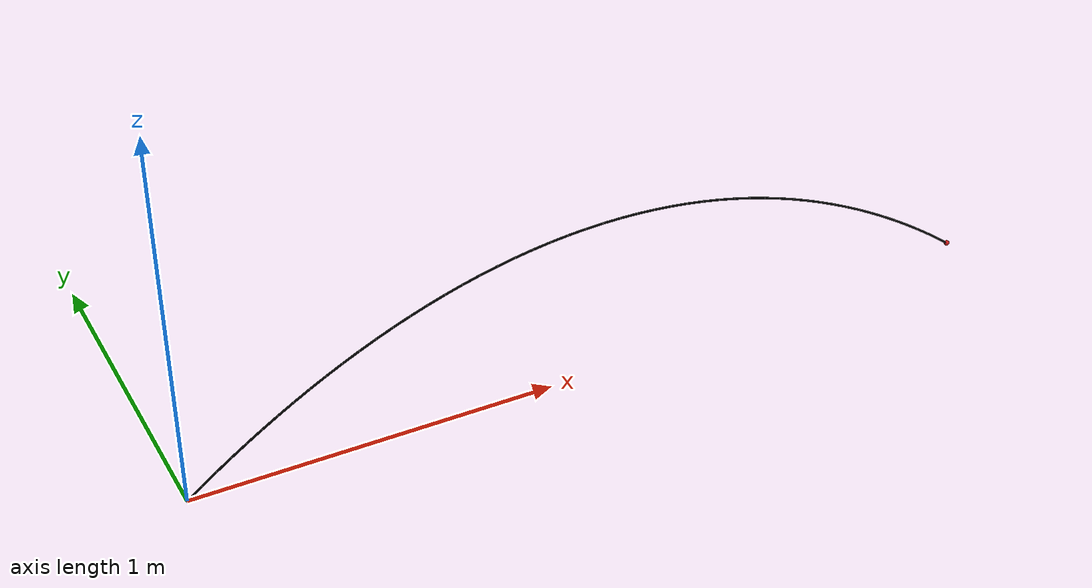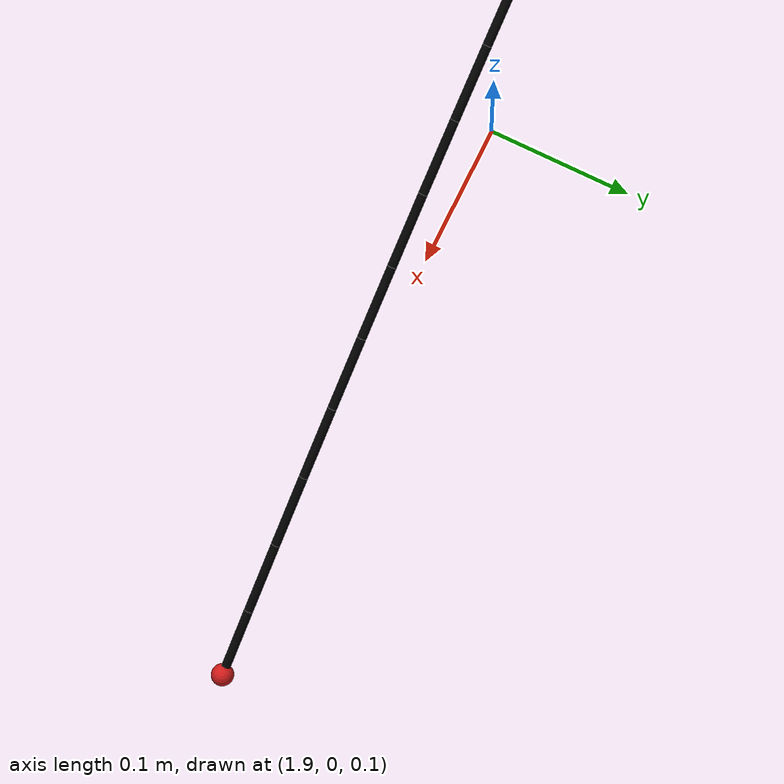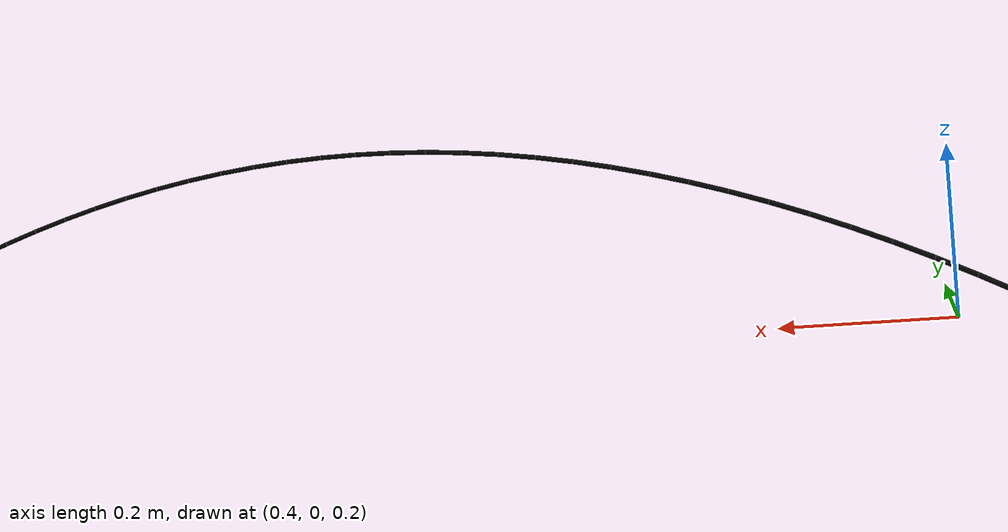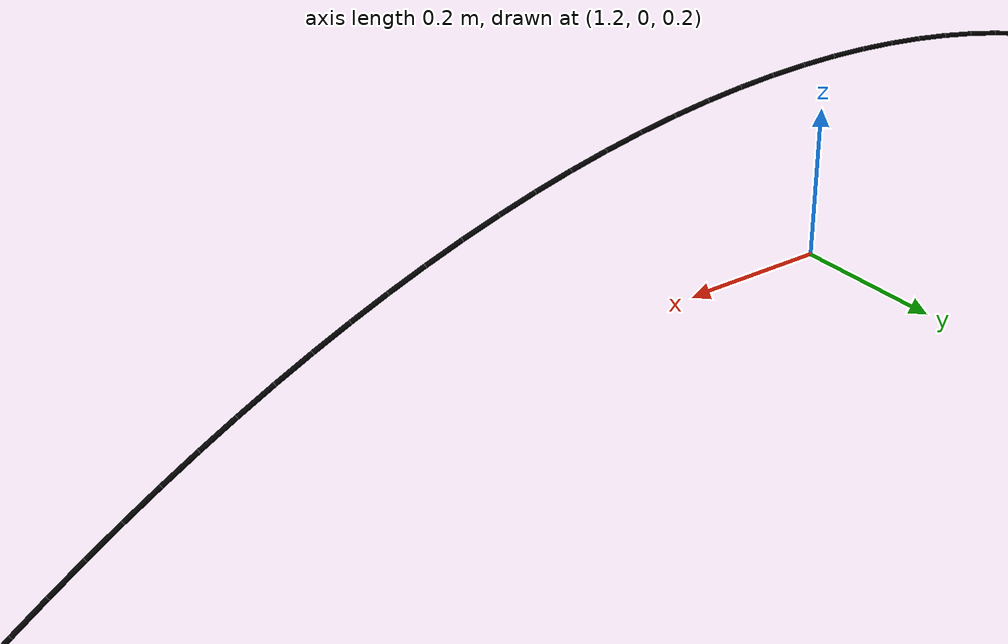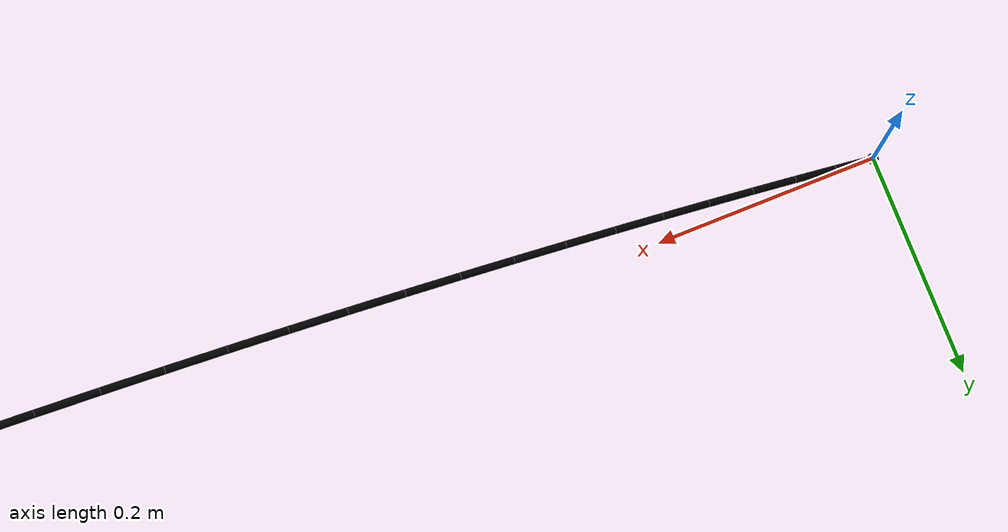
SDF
<?xml version="1.0" ?>
<sdf version="1.8">
  <model name="cabo">
    <self_collide>false</self_collide>

    <plugin filename="gz-sim-joint-state-publisher-system" name="gz::sim::systems::JointStatePublisher"/>

    <link name="raiz_cabo">
      <pose>0 0 0 0 0 0</pose>
      <inertial>
        <mass>0.02</mass>
        <inertia>
          <ixx>1e-05</ixx><ixy>0</ixy><ixz>0</ixz>
          <iyy>1e-05</iyy><iyz>0</iyz><izz>1e-05</izz>
        </inertia>
      </inertial>
      <visual name="visual_raiz">
        <geometry><sphere><radius>0.005</radius></sphere></geometry>
        <material>
          <ambient>0.1 0.1 0.1 1</ambient>
          <diffuse>0.1 0.1 0.1 1</diffuse>
        </material>
      </visual>
    </link>

      <link name="segment_1">
        <pose>0.000000 0.000000 0.000000 0 -0.653225 0.000000</pose>
        <enable_wind>false</enable_wind>
        <self_collide>false</self_collide>

        <visual name="visual">
          <pose>0.025000 0 0 0 1.5708 0</pose>
          <geometry><cylinder><radius>0.003</radius><length>0.050000</length></cylinder></geometry>
          <material>
            <ambient>0 0 0 1</ambient>
            <diffuse>0 0 0 1</diffuse>
          </material>
        </visual>
        <collision name="collision">
          <pose>0.025000 0 0 0 1.5708 0</pose>
          <geometry><cylinder><radius>0.0015</radius><length>0.030000</length></cylinder></geometry>
        </collision>

        <inertial>
          <pose>0.025000 0 0 0 0 0</pose>
          <mass>0.002000000000000001</mass>
          <inertia>
            <ixx>1e-05</ixx><ixy>0</ixy><ixz>0</ixz>
            <iyy>1e-05</iyy><iyz>0</iyz><izz>1e-05</izz>
          </inertia>
        </inertial>
      </link>

      <joint name="joint_1" type="universal">
        <parent>raiz_cabo</parent>
        <child>segment_1</child>
        <pose>0 0 0 0 0 0</pose>
        <axis>
          <xyz>0 1 0</xyz>
        <limit>
          <lower>-0.523599</lower>
          <upper>0.523599</upper>
        </limit>

          <dynamics>
            <damping>0.002</damping>
            <friction>0.0</friction>
          </dynamics>
        </axis>
        <axis2>
          <xyz>0 0 1</xyz>
        <limit>
          <lower>-0.523599</lower>
          <upper>0.523599</upper>
        </limit>

          <dynamics>
            <damping>0.002</damping>
            <friction>0.0</friction>
          </dynamics>
        </axis2>

      <sensor name="sensor_tensao_ancora" type="force_torque">
        <always_on>true</always_on>
        <update_rate>50</update_rate>
        <topic>/cabo/tensao_ancora</topic>
      </sensor>
      </joint>

      <link name="segment_2">
        <pose>0.039706 0.000000 0.030388 0 -0.636634 0.000000</pose>
        <enable_wind>false</enable_wind>
        <self_collide>false</self_collide>

        <visual name="visual">
          <pose>0.025000 0 0 0 1.5708 0</pose>
          <geometry><cylinder><radius>0.003</radius><length>0.050000</length></cylinder></geometry>
          <material>
            <ambient>0 0 0 1</ambient>
            <diffuse>0 0 0 1</diffuse>
          </material>
        </visual>
        <collision name="collision">
          <pose>0.025000 0 0 0 1.5708 0</pose>
          <geometry><cylinder><radius>0.0015</radius><length>0.030000</length></cylinder></geometry>
        </collision>

        <inertial>
          <pose>0.025000 0 0 0 0 0</pose>
          <mass>0.002</mass>
          <inertia>
            <ixx>1e-05</ixx><ixy>0</ixy><ixz>0</ixz>
            <iyy>1e-05</iyy><iyz>0</iyz><izz>1e-05</izz>
          </inertia>
        </inertial>
      </link>

      <joint name="joint_2" type="universal">
        <parent>segment_1</parent>
        <child>segment_2</child>
        <pose>0 0 0 0 0 0</pose>
        <axis>
          <xyz>0 1 0</xyz>
        <limit>
          <lower>-0.523599</lower>
          <upper>0.523599</upper>
        </limit>

          <dynamics>
            <damping>0.002</damping>
            <friction>0.0</friction>
          </dynamics>
        </axis>
        <axis2>
          <xyz>0 0 1</xyz>
        <limit>
          <lower>-0.523599</lower>
          <upper>0.523599</upper>
        </limit>

          <dynamics>
            <damping>0.002</damping>
            <friction>0.0</friction>
          </dynamics>
        </axis2>

      </joint>

      <link name="segment_3">
        <pose>0.079911 0.000000 0.060112 0 -0.619409 0.000000</pose>
        <enable_wind>false</enable_wind>
        <self_collide>false</self_collide>

        <visual name="visual">
          <pose>0.025000 0 0 0 1.5708 0</pose>
          <geometry><cylinder><radius>0.003</radius><length>0.050000</length></cylinder></geometry>
          <material>
            <ambient>0 0 0 1</ambient>
            <diffuse>0 0 0 1</diffuse>
          </material>
        </visual>
        <collision name="collision">
          <pose>0.025000 0 0 0 1.5708 0</pose>
          <geometry><cylinder><radius>0.0015</radius><length>0.030000</length></cylinder></geometry>
        </collision>

        <inertial>
          <pose>0.025000 0 0 0 0 0</pose>
          <mass>0.0019999999999999996</mass>
          <inertia>
            <ixx>1e-05</ixx><ixy>0</ixy><ixz>0</ixz>
            <iyy>1e-05</iyy><iyz>0</iyz><izz>1e-05</izz>
          </inertia>
        </inertial>
      </link>

      <joint name="joint_3" type="universal">
        <parent>segment_2</parent>
        <child>segment_3</child>
        <pose>0 0 0 0 0 0</pose>
        <axis>
          <xyz>0 1 0</xyz>
        <limit>
          <lower>-0.523599</lower>
          <upper>0.523599</upper>
        </limit>

          <dynamics>
            <damping>0.002</damping>
            <friction>0.0</friction>
          </dynamics>
        </axis>
        <axis2>
          <xyz>0 0 1</xyz>
        <limit>
          <lower>-0.523599</lower>
          <upper>0.523599</upper>
        </limit>

          <dynamics>
            <damping>0.002</damping>
            <friction>0.0</friction>
          </dynamics>
        </axis2>

      </joint>

      <link name="segment_4">
        <pose>0.120623 0.000000 0.089140 0 -0.601526 0.000000</pose>
        <enable_wind>false</enable_wind>
        <self_collide>false</self_collide>

        <visual name="visual">
          <pose>0.025000 0 0 0 1.5708 0</pose>
          <geometry><cylinder><radius>0.003</radius><length>0.050000</length></cylinder></geometry>
          <material>
            <ambient>0 0 0 1</ambient>
            <diffuse>0 0 0 1</diffuse>
          </material>
        </visual>
        <collision name="collision">
          <pose>0.025000 0 0 0 1.5708 0</pose>
          <geometry><cylinder><radius>0.0015</radius><length>0.030000</length></cylinder></geometry>
        </collision>

        <inertial>
          <pose>0.025000 0 0 0 0 0</pose>
          <mass>0.0019999999999999987</mass>
          <inertia>
            <ixx>1e-05</ixx><ixy>0</ixy><ixz>0</ixz>
            <iyy>1e-05</iyy><iyz>0</iyz><izz>1e-05</izz>
          </inertia>
        </inertial>
      </link>

      <joint name="joint_4" type="universal">
        <parent>segment_3</parent>
        <child>segment_4</child>
        <pose>0 0 0 0 0 0</pose>
        <axis>
          <xyz>0 1 0</xyz>
        <limit>
          <lower>-0.523599</lower>
          <upper>0.523599</upper>
        </limit>

          <dynamics>
            <damping>0.002</damping>
            <friction>0.0</friction>
          </dynamics>
        </axis>
        <axis2>
          <xyz>0 0 1</xyz>
        <limit>
          <lower>-0.523599</lower>
          <upper>0.523599</upper>
        </limit>

          <dynamics>
            <damping>0.002</damping>
            <friction>0.0</friction>
          </dynamics>
        </axis2>

      </joint>

      <link name="segment_5">
        <pose>0.161846 0.000000 0.117435 0 -0.582958 0.000000</pose>
        <enable_wind>false</enable_wind>
        <self_collide>false</self_collide>

        <visual name="visual">
          <pose>0.025000 0 0 0 1.5708 0</pose>
          <geometry><cylinder><radius>0.003</radius><length>0.050000</length></cylinder></geometry>
          <material>
            <ambient>0 0 0 1</ambient>
            <diffuse>0 0 0 1</diffuse>
          </material>
        </visual>
        <collision name="collision">
          <pose>0.025000 0 0 0 1.5708 0</pose>
          <geometry><cylinder><radius>0.0015</radius><length>0.030000</length></cylinder></geometry>
        </collision>

        <inertial>
          <pose>0.025000 0 0 0 0 0</pose>
          <mass>0.002</mass>
          <inertia>
            <ixx>1e-05</ixx><ixy>0</ixy><ixz>0</ixz>
            <iyy>1e-05</iyy><iyz>0</iyz><izz>1e-05</izz>
          </inertia>
        </inertial>
      </link>

      <joint name="joint_5" type="universal">
        <parent>segment_4</parent>
        <child>segment_5</child>
        <pose>0 0 0 0 0 0</pose>
        <axis>
          <xyz>0 1 0</xyz>
        <limit>
          <lower>-0.523599</lower>
          <upper>0.523599</upper>
        </limit>

          <dynamics>
            <damping>0.002</damping>
            <friction>0.0</friction>
          </dynamics>
        </axis>
        <axis2>
          <xyz>0 0 1</xyz>
        <limit>
          <lower>-0.523599</lower>
          <upper>0.523599</upper>
        </limit>

          <dynamics>
            <damping>0.002</damping>
            <friction>0.0</friction>
          </dynamics>
        </axis2>

      </joint>

      <link name="segment_6">
        <pose>0.203588 0.000000 0.144960 0 -0.563683 0.000000</pose>
        <enable_wind>false</enable_wind>
        <self_collide>false</self_collide>

        <visual name="visual">
          <pose>0.025000 0 0 0 1.5708 0</pose>
          <geometry><cylinder><radius>0.003</radius><length>0.050000</length></cylinder></geometry>
          <material>
            <ambient>0 0 0 1</ambient>
            <diffuse>0 0 0 1</diffuse>
          </material>
        </visual>
        <collision name="collision">
          <pose>0.025000 0 0 0 1.5708 0</pose>
          <geometry><cylinder><radius>0.0015</radius><length>0.030000</length></cylinder></geometry>
        </collision>

        <inertial>
          <pose>0.025000 0 0 0 0 0</pose>
          <mass>0.002000000000000001</mass>
          <inertia>
            <ixx>1e-05</ixx><ixy>0</ixy><ixz>0</ixz>
            <iyy>1e-05</iyy><iyz>0</iyz><izz>1e-05</izz>
          </inertia>
        </inertial>
      </link>

      <joint name="joint_6" type="universal">
        <parent>segment_5</parent>
        <child>segment_6</child>
        <pose>0 0 0 0 0 0</pose>
        <axis>
          <xyz>0 1 0</xyz>
        <limit>
          <lower>-0.523599</lower>
          <upper>0.523599</upper>
        </limit>

          <dynamics>
            <damping>0.002</damping>
            <friction>0.0</friction>
          </dynamics>
        </axis>
        <axis2>
          <xyz>0 0 1</xyz>
        <limit>
          <lower>-0.523599</lower>
          <upper>0.523599</upper>
        </limit>

          <dynamics>
            <damping>0.002</damping>
            <friction>0.0</friction>
          </dynamics>
        </axis2>

      </joint>

      <link name="segment_7">
        <pose>0.245853 0.000000 0.171675 0 -0.543677 0.000000</pose>
        <enable_wind>false</enable_wind>
        <self_collide>false</self_collide>

        <visual name="visual">
          <pose>0.025000 0 0 0 1.5708 0</pose>
          <geometry><cylinder><radius>0.003</radius><length>0.050000</length></cylinder></geometry>
          <material>
            <ambient>0 0 0 1</ambient>
            <diffuse>0 0 0 1</diffuse>
          </material>
        </visual>
        <collision name="collision">
          <pose>0.025000 0 0 0 1.5708 0</pose>
          <geometry><cylinder><radius>0.0015</radius><length>0.030000</length></cylinder></geometry>
        </collision>

        <inertial>
          <pose>0.025000 0 0 0 0 0</pose>
          <mass>0.0019999999999999983</mass>
          <inertia>
            <ixx>1e-05</ixx><ixy>0</ixy><ixz>0</ixz>
            <iyy>1e-05</iyy><iyz>0</iyz><izz>1e-05</izz>
          </inertia>
        </inertial>
      </link>

      <joint name="joint_7" type="universal">
        <parent>segment_6</parent>
        <child>segment_7</child>
        <pose>0 0 0 0 0 0</pose>
        <axis>
          <xyz>0 1 0</xyz>
        <limit>
          <lower>-0.523599</lower>
          <upper>0.523599</upper>
        </limit>

          <dynamics>
            <damping>0.002</damping>
            <friction>0.0</friction>
          </dynamics>
        </axis>
        <axis2>
          <xyz>0 0 1</xyz>
        <limit>
          <lower>-0.523599</lower>
          <upper>0.523599</upper>
        </limit>

          <dynamics>
            <damping>0.002</damping>
            <friction>0.0</friction>
          </dynamics>
        </axis2>

      </joint>

      <link name="segment_8">
        <pose>0.288643 0.000000 0.197539 0 -0.522918 0.000000</pose>
        <enable_wind>false</enable_wind>
        <self_collide>false</self_collide>

        <visual name="visual">
          <pose>0.025000 0 0 0 1.5708 0</pose>
          <geometry><cylinder><radius>0.003</radius><length>0.050000</length></cylinder></geometry>
          <material>
            <ambient>0 0 0 1</ambient>
            <diffuse>0 0 0 1</diffuse>
          </material>
        </visual>
        <collision name="collision">
          <pose>0.025000 0 0 0 1.5708 0</pose>
          <geometry><cylinder><radius>0.0015</radius><length>0.030000</length></cylinder></geometry>
        </collision>

        <inertial>
          <pose>0.025000 0 0 0 0 0</pose>
          <mass>0.002000000000000002</mass>
          <inertia>
            <ixx>1e-05</ixx><ixy>0</ixy><ixz>0</ixz>
            <iyy>1e-05</iyy><iyz>0</iyz><izz>1e-05</izz>
          </inertia>
        </inertial>
      </link>

      <joint name="joint_8" type="universal">
        <parent>segment_7</parent>
        <child>segment_8</child>
        <pose>0 0 0 0 0 0</pose>
        <axis>
          <xyz>0 1 0</xyz>
        <limit>
          <lower>-0.523599</lower>
          <upper>0.523599</upper>
        </limit>

          <dynamics>
            <damping>0.002</damping>
            <friction>0.0</friction>
          </dynamics>
        </axis>
        <axis2>
          <xyz>0 0 1</xyz>
        <limit>
          <lower>-0.523599</lower>
          <upper>0.523599</upper>
        </limit>

          <dynamics>
            <damping>0.002</damping>
            <friction>0.0</friction>
          </dynamics>
        </axis2>

      </joint>

      <link name="segment_9">
        <pose>0.331962 0.000000 0.222510 0 -0.501387 0.000000</pose>
        <enable_wind>false</enable_wind>
        <self_collide>false</self_collide>

        <visual name="visual">
          <pose>0.025000 0 0 0 1.5708 0</pose>
          <geometry><cylinder><radius>0.003</radius><length>0.050000</length></cylinder></geometry>
          <material>
            <ambient>0 0 0 1</ambient>
            <diffuse>0 0 0 1</diffuse>
          </material>
        </visual>
        <collision name="collision">
          <pose>0.025000 0 0 0 1.5708 0</pose>
          <geometry><cylinder><radius>0.0015</radius><length>0.030000</length></cylinder></geometry>
        </collision>

        <inertial>
          <pose>0.025000 0 0 0 0 0</pose>
          <mass>0.0020000000000000013</mass>
          <inertia>
            <ixx>1e-05</ixx><ixy>0</ixy><ixz>0</ixz>
            <iyy>1e-05</iyy><iyz>0</iyz><izz>1e-05</izz>
          </inertia>
        </inertial>
      </link>

      <joint name="joint_9" type="universal">
        <parent>segment_8</parent>
        <child>segment_9</child>
        <pose>0 0 0 0 0 0</pose>
        <axis>
          <xyz>0 1 0</xyz>
        <limit>
          <lower>-0.523599</lower>
          <upper>0.523599</upper>
        </limit>

          <dynamics>
            <damping>0.002</damping>
            <friction>0.0</friction>
          </dynamics>
        </axis>
        <axis2>
          <xyz>0 0 1</xyz>
        <limit>
          <lower>-0.523599</lower>
          <upper>0.523599</upper>
        </limit>

          <dynamics>
            <damping>0.002</damping>
            <friction>0.0</friction>
          </dynamics>
        </axis2>

      </joint>

      <link name="segment_10">
        <pose>0.375807 0.000000 0.246542 0 -0.479065 0.000000</pose>
        <enable_wind>false</enable_wind>
        <self_collide>false</self_collide>

        <visual name="visual">
          <pose>0.025000 0 0 0 1.5708 0</pose>
          <geometry><cylinder><radius>0.003</radius><length>0.050000</length></cylinder></geometry>
          <material>
            <ambient>0 0 0 1</ambient>
            <diffuse>0 0 0 1</diffuse>
          </material>
        </visual>
        <collision name="collision">
          <pose>0.025000 0 0 0 1.5708 0</pose>
          <geometry><cylinder><radius>0.0015</radius><length>0.030000</length></cylinder></geometry>
        </collision>

        <inertial>
          <pose>0.025000 0 0 0 0 0</pose>
          <mass>0.001999999999999998</mass>
          <inertia>
            <ixx>1e-05</ixx><ixy>0</ixy><ixz>0</ixz>
            <iyy>1e-05</iyy><iyz>0</iyz><izz>1e-05</izz>
          </inertia>
        </inertial>
      </link>

      <joint name="joint_10" type="universal">
        <parent>segment_9</parent>
        <child>segment_10</child>
        <pose>0 0 0 0 0 0</pose>
        <axis>
          <xyz>0 1 0</xyz>
        <limit>
          <lower>-0.523599</lower>
          <upper>0.523599</upper>
        </limit>

          <dynamics>
            <damping>0.002</damping>
            <friction>0.0</friction>
          </dynamics>
        </axis>
        <axis2>
          <xyz>0 0 1</xyz>
        <limit>
          <lower>-0.523599</lower>
          <upper>0.523599</upper>
        </limit>

          <dynamics>
            <damping>0.002</damping>
            <friction>0.0</friction>
          </dynamics>
        </axis2>

      </joint>

      <link name="segment_11">
        <pose>0.420179 0.000000 0.269589 0 -0.455939 0.000000</pose>
        <enable_wind>false</enable_wind>
        <self_collide>false</self_collide>

        <visual name="visual">
          <pose>0.025000 0 0 0 1.5708 0</pose>
          <geometry><cylinder><radius>0.003</radius><length>0.050000</length></cylinder></geometry>
          <material>
            <ambient>0 0 0 1</ambient>
            <diffuse>0 0 0 1</diffuse>
          </material>
        </visual>
        <collision name="collision">
          <pose>0.025000 0 0 0 1.5708 0</pose>
          <geometry><cylinder><radius>0.0015</radius><length>0.030000</length></cylinder></geometry>
        </collision>

        <inertial>
          <pose>0.025000 0 0 0 0 0</pose>
          <mass>0.0019999999999999983</mass>
          <inertia>
            <ixx>1e-05</ixx><ixy>0</ixy><ixz>0</ixz>
            <iyy>1e-05</iyy><iyz>0</iyz><izz>1e-05</izz>
          </inertia>
        </inertial>
      </link>

      <joint name="joint_11" type="universal">
        <parent>segment_10</parent>
        <child>segment_11</child>
        <pose>0 0 0 0 0 0</pose>
        <axis>
          <xyz>0 1 0</xyz>
        <limit>
          <lower>-0.523599</lower>
          <upper>0.523599</upper>
        </limit>

          <dynamics>
            <damping>0.002</damping>
            <friction>0.0</friction>
          </dynamics>
        </axis>
        <axis2>
          <xyz>0 0 1</xyz>
        <limit>
          <lower>-0.523599</lower>
          <upper>0.523599</upper>
        </limit>

          <dynamics>
            <damping>0.002</damping>
            <friction>0.0</friction>
          </dynamics>
        </axis2>

      </joint>

      <link name="segment_12">
        <pose>0.465071 0.000000 0.291605 0 -0.431999 0.000000</pose>
        <enable_wind>false</enable_wind>
        <self_collide>false</self_collide>

        <visual name="visual">
          <pose>0.025000 0 0 0 1.5708 0</pose>
          <geometry><cylinder><radius>0.003</radius><length>0.050000</length></cylinder></geometry>
          <material>
            <ambient>0 0 0 1</ambient>
            <diffuse>0 0 0 1</diffuse>
          </material>
        </visual>
        <collision name="collision">
          <pose>0.025000 0 0 0 1.5708 0</pose>
          <geometry><cylinder><radius>0.0015</radius><length>0.030000</length></cylinder></geometry>
        </collision>

        <inertial>
          <pose>0.025000 0 0 0 0 0</pose>
          <mass>0.001999999999999997</mass>
          <inertia>
            <ixx>1e-05</ixx><ixy>0</ixy><ixz>0</ixz>
            <iyy>1e-05</iyy><iyz>0</iyz><izz>1e-05</izz>
          </inertia>
        </inertial>
      </link>

      <joint name="joint_12" type="universal">
        <parent>segment_11</parent>
        <child>segment_12</child>
        <pose>0 0 0 0 0 0</pose>
        <axis>
          <xyz>0 1 0</xyz>
        <limit>
          <lower>-0.523599</lower>
          <upper>0.523599</upper>
        </limit>

          <dynamics>
            <damping>0.002</damping>
            <friction>0.0</friction>
          </dynamics>
        </axis>
        <axis2>
          <xyz>0 0 1</xyz>
        <limit>
          <lower>-0.523599</lower>
          <upper>0.523599</upper>
        </limit>

          <dynamics>
            <damping>0.002</damping>
            <friction>0.0</friction>
          </dynamics>
        </axis2>

      </joint>

      <link name="segment_13">
        <pose>0.510478 0.000000 0.312539 0 -0.407240 0.000000</pose>
        <enable_wind>false</enable_wind>
        <self_collide>false</self_collide>

        <visual name="visual">
          <pose>0.025000 0 0 0 1.5708 0</pose>
          <geometry><cylinder><radius>0.003</radius><length>0.050000</length></cylinder></geometry>
          <material>
            <ambient>0 0 0 1</ambient>
            <diffuse>0 0 0 1</diffuse>
          </material>
        </visual>
        <collision name="collision">
          <pose>0.025000 0 0 0 1.5708 0</pose>
          <geometry><cylinder><radius>0.0015</radius><length>0.030000</length></cylinder></geometry>
        </collision>

        <inertial>
          <pose>0.025000 0 0 0 0 0</pose>
          <mass>0.0019999999999999996</mass>
          <inertia>
            <ixx>1e-05</ixx><ixy>0</ixy><ixz>0</ixz>
            <iyy>1e-05</iyy><iyz>0</iyz><izz>1e-05</izz>
          </inertia>
        </inertial>
      </link>

      <joint name="joint_13" type="universal">
        <parent>segment_12</parent>
        <child>segment_13</child>
        <pose>0 0 0 0 0 0</pose>
        <axis>
          <xyz>0 1 0</xyz>
        <limit>
          <lower>-0.523599</lower>
          <upper>0.523599</upper>
        </limit>

          <dynamics>
            <damping>0.002</damping>
            <friction>0.0</friction>
          </dynamics>
        </axis>
        <axis2>
          <xyz>0 0 1</xyz>
        <limit>
          <lower>-0.523599</lower>
          <upper>0.523599</upper>
        </limit>

          <dynamics>
            <damping>0.002</damping>
            <friction>0.0</friction>
          </dynamics>
        </axis2>

      </joint>

      <link name="segment_14">
        <pose>0.556389 0.000000 0.332343 0 -0.381662 0.000000</pose>
        <enable_wind>false</enable_wind>
        <self_collide>false</self_collide>

        <visual name="visual">
          <pose>0.025000 0 0 0 1.5708 0</pose>
          <geometry><cylinder><radius>0.003</radius><length>0.050000</length></cylinder></geometry>
          <material>
            <ambient>0 0 0 1</ambient>
            <diffuse>0 0 0 1</diffuse>
          </material>
        </visual>
        <collision name="collision">
          <pose>0.025000 0 0 0 1.5708 0</pose>
          <geometry><cylinder><radius>0.0015</radius><length>0.030000</length></cylinder></geometry>
        </collision>

        <inertial>
          <pose>0.025000 0 0 0 0 0</pose>
          <mass>0.002000000000000004</mass>
          <inertia>
            <ixx>1e-05</ixx><ixy>0</ixy><ixz>0</ixz>
            <iyy>1e-05</iyy><iyz>0</iyz><izz>1e-05</izz>
          </inertia>
        </inertial>
      </link>

      <joint name="joint_14" type="universal">
        <parent>segment_13</parent>
        <child>segment_14</child>
        <pose>0 0 0 0 0 0</pose>
        <axis>
          <xyz>0 1 0</xyz>
        <limit>
          <lower>-0.523599</lower>
          <upper>0.523599</upper>
        </limit>

          <dynamics>
            <damping>0.002</damping>
            <friction>0.0</friction>
          </dynamics>
        </axis>
        <axis2>
          <xyz>0 0 1</xyz>
        <limit>
          <lower>-0.523599</lower>
          <upper>0.523599</upper>
        </limit>

          <dynamics>
            <damping>0.002</damping>
            <friction>0.0</friction>
          </dynamics>
        </axis2>

      </joint>

      <link name="segment_15">
        <pose>0.602791 0.000000 0.350966 0 -0.355271 0.000000</pose>
        <enable_wind>false</enable_wind>
        <self_collide>false</self_collide>

        <visual name="visual">
          <pose>0.025000 0 0 0 1.5708 0</pose>
          <geometry><cylinder><radius>0.003</radius><length>0.050000</length></cylinder></geometry>
          <material>
            <ambient>0 0 0 1</ambient>
            <diffuse>0 0 0 1</diffuse>
          </material>
        </visual>
        <collision name="collision">
          <pose>0.025000 0 0 0 1.5708 0</pose>
          <geometry><cylinder><radius>0.0015</radius><length>0.030000</length></cylinder></geometry>
        </collision>

        <inertial>
          <pose>0.025000 0 0 0 0 0</pose>
          <mass>0.001999999999999998</mass>
          <inertia>
            <ixx>1e-05</ixx><ixy>0</ixy><ixz>0</ixz>
            <iyy>1e-05</iyy><iyz>0</iyz><izz>1e-05</izz>
          </inertia>
        </inertial>
      </link>

      <joint name="joint_15" type="universal">
        <parent>segment_14</parent>
        <child>segment_15</child>
        <pose>0 0 0 0 0 0</pose>
        <axis>
          <xyz>0 1 0</xyz>
        <limit>
          <lower>-0.523599</lower>
          <upper>0.523599</upper>
        </limit>

          <dynamics>
            <damping>0.002</damping>
            <friction>0.0</friction>
          </dynamics>
        </axis>
        <axis2>
          <xyz>0 0 1</xyz>
        <limit>
          <lower>-0.523599</lower>
          <upper>0.523599</upper>
        </limit>

          <dynamics>
            <damping>0.002</damping>
            <friction>0.0</friction>
          </dynamics>
        </axis2>

      </joint>

      <link name="segment_16">
        <pose>0.649668 0.000000 0.368358 0 -0.328082 0.000000</pose>
        <enable_wind>false</enable_wind>
        <self_collide>false</self_collide>

        <visual name="visual">
          <pose>0.025000 0 0 0 1.5708 0</pose>
          <geometry><cylinder><radius>0.003</radius><length>0.050000</length></cylinder></geometry>
          <material>
            <ambient>0 0 0 1</ambient>
            <diffuse>0 0 0 1</diffuse>
          </material>
        </visual>
        <collision name="collision">
          <pose>0.025000 0 0 0 1.5708 0</pose>
          <geometry><cylinder><radius>0.0015</radius><length>0.030000</length></cylinder></geometry>
        </collision>

        <inertial>
          <pose>0.025000 0 0 0 0 0</pose>
          <mass>0.001999999999999998</mass>
          <inertia>
            <ixx>1e-05</ixx><ixy>0</ixy><ixz>0</ixz>
            <iyy>1e-05</iyy><iyz>0</iyz><izz>1e-05</izz>
          </inertia>
        </inertial>
      </link>

      <joint name="joint_16" type="universal">
        <parent>segment_15</parent>
        <child>segment_16</child>
        <pose>0 0 0 0 0 0</pose>
        <axis>
          <xyz>0 1 0</xyz>
        <limit>
          <lower>-0.523599</lower>
          <upper>0.523599</upper>
        </limit>

          <dynamics>
            <damping>0.002</damping>
            <friction>0.0</friction>
          </dynamics>
        </axis>
        <axis2>
          <xyz>0 0 1</xyz>
        <limit>
          <lower>-0.523599</lower>
          <upper>0.523599</upper>
        </limit>

          <dynamics>
            <damping>0.002</damping>
            <friction>0.0</friction>
          </dynamics>
        </axis2>

      </joint>

      <link name="segment_17">
        <pose>0.697002 0.000000 0.384470 0 -0.300117 0.000000</pose>
        <enable_wind>false</enable_wind>
        <self_collide>false</self_collide>

        <visual name="visual">
          <pose>0.025000 0 0 0 1.5708 0</pose>
          <geometry><cylinder><radius>0.003</radius><length>0.050000</length></cylinder></geometry>
          <material>
            <ambient>0 0 0 1</ambient>
            <diffuse>0 0 0 1</diffuse>
          </material>
        </visual>
        <collision name="collision">
          <pose>0.025000 0 0 0 1.5708 0</pose>
          <geometry><cylinder><radius>0.0015</radius><length>0.030000</length></cylinder></geometry>
        </collision>

        <inertial>
          <pose>0.025000 0 0 0 0 0</pose>
          <mass>0.0020000000000000018</mass>
          <inertia>
            <ixx>1e-05</ixx><ixy>0</ixy><ixz>0</ixz>
            <iyy>1e-05</iyy><iyz>0</iyz><izz>1e-05</izz>
          </inertia>
        </inertial>
      </link>

      <joint name="joint_17" type="universal">
        <parent>segment_16</parent>
        <child>segment_17</child>
        <pose>0 0 0 0 0 0</pose>
        <axis>
          <xyz>0 1 0</xyz>
        <limit>
          <lower>-0.523599</lower>
          <upper>0.523599</upper>
        </limit>

          <dynamics>
            <damping>0.002</damping>
            <friction>0.0</friction>
          </dynamics>
        </axis>
        <axis2>
          <xyz>0 0 1</xyz>
        <limit>
          <lower>-0.523599</lower>
          <upper>0.523599</upper>
        </limit>

          <dynamics>
            <damping>0.002</damping>
            <friction>0.0</friction>
          </dynamics>
        </axis2>

      </joint>

      <link name="segment_18">
        <pose>0.744767 0.000000 0.399251 0 -0.271408 0.000000</pose>
        <enable_wind>false</enable_wind>
        <self_collide>false</self_collide>

        <visual name="visual">
          <pose>0.025000 0 0 0 1.5708 0</pose>
          <geometry><cylinder><radius>0.003</radius><length>0.050000</length></cylinder></geometry>
          <material>
            <ambient>0 0 0 1</ambient>
            <diffuse>0 0 0 1</diffuse>
          </material>
        </visual>
        <collision name="collision">
          <pose>0.025000 0 0 0 1.5708 0</pose>
          <geometry><cylinder><radius>0.0015</radius><length>0.030000</length></cylinder></geometry>
        </collision>

        <inertial>
          <pose>0.025000 0 0 0 0 0</pose>
          <mass>0.0019999999999999966</mass>
          <inertia>
            <ixx>1e-05</ixx><ixy>0</ixy><ixz>0</ixz>
            <iyy>1e-05</iyy><iyz>0</iyz><izz>1e-05</izz>
          </inertia>
        </inertial>
      </link>

      <joint name="joint_18" type="universal">
        <parent>segment_17</parent>
        <child>segment_18</child>
        <pose>0 0 0 0 0 0</pose>
        <axis>
          <xyz>0 1 0</xyz>
        <limit>
          <lower>-0.523599</lower>
          <upper>0.523599</upper>
        </limit>

          <dynamics>
            <damping>0.002</damping>
            <friction>0.0</friction>
          </dynamics>
        </axis>
        <axis2>
          <xyz>0 0 1</xyz>
        <limit>
          <lower>-0.523599</lower>
          <upper>0.523599</upper>
        </limit>

          <dynamics>
            <damping>0.002</damping>
            <friction>0.0</friction>
          </dynamics>
        </axis2>

      </joint>

      <link name="segment_19">
        <pose>0.792936 0.000000 0.412656 0 -0.241994 0.000000</pose>
        <enable_wind>false</enable_wind>
        <self_collide>false</self_collide>

        <visual name="visual">
          <pose>0.025000 0 0 0 1.5708 0</pose>
          <geometry><cylinder><radius>0.003</radius><length>0.050000</length></cylinder></geometry>
          <material>
            <ambient>0 0 0 1</ambient>
            <diffuse>0 0 0 1</diffuse>
          </material>
        </visual>
        <collision name="collision">
          <pose>0.025000 0 0 0 1.5708 0</pose>
          <geometry><cylinder><radius>0.0015</radius><length>0.030000</length></cylinder></geometry>
        </collision>

        <inertial>
          <pose>0.025000 0 0 0 0 0</pose>
          <mass>0.0020000000000000035</mass>
          <inertia>
            <ixx>1e-05</ixx><ixy>0</ixy><ixz>0</ixz>
            <iyy>1e-05</iyy><iyz>0</iyz><izz>1e-05</izz>
          </inertia>
        </inertial>
      </link>

      <joint name="joint_19" type="universal">
        <parent>segment_18</parent>
        <child>segment_19</child>
        <pose>0 0 0 0 0 0</pose>
        <axis>
          <xyz>0 1 0</xyz>
        <limit>
          <lower>-0.523599</lower>
          <upper>0.523599</upper>
        </limit>

          <dynamics>
            <damping>0.002</damping>
            <friction>0.0</friction>
          </dynamics>
        </axis>
        <axis2>
          <xyz>0 0 1</xyz>
        <limit>
          <lower>-0.523599</lower>
          <upper>0.523599</upper>
        </limit>

          <dynamics>
            <damping>0.002</damping>
            <friction>0.0</friction>
          </dynamics>
        </axis2>

      </joint>

      <link name="segment_20">
        <pose>0.841480 0.000000 0.424638 0 -0.211925 0.000000</pose>
        <enable_wind>false</enable_wind>
        <self_collide>false</self_collide>

        <visual name="visual">
          <pose>0.025000 0 0 0 1.5708 0</pose>
          <geometry><cylinder><radius>0.003</radius><length>0.050000</length></cylinder></geometry>
          <material>
            <ambient>0 0 0 1</ambient>
            <diffuse>0 0 0 1</diffuse>
          </material>
        </visual>
        <collision name="collision">
          <pose>0.025000 0 0 0 1.5708 0</pose>
          <geometry><cylinder><radius>0.0015</radius><length>0.030000</length></cylinder></geometry>
        </collision>

        <inertial>
          <pose>0.025000 0 0 0 0 0</pose>
          <mass>0.0019999999999999996</mass>
          <inertia>
            <ixx>1e-05</ixx><ixy>0</ixy><ixz>0</ixz>
            <iyy>1e-05</iyy><iyz>0</iyz><izz>1e-05</izz>
          </inertia>
        </inertial>
      </link>

      <joint name="joint_20" type="universal">
        <parent>segment_19</parent>
        <child>segment_20</child>
        <pose>0 0 0 0 0 0</pose>
        <axis>
          <xyz>0 1 0</xyz>
        <limit>
          <lower>-0.523599</lower>
          <upper>0.523599</upper>
        </limit>

          <dynamics>
            <damping>0.002</damping>
            <friction>0.0</friction>
          </dynamics>
        </axis>
        <axis2>
          <xyz>0 0 1</xyz>
        <limit>
          <lower>-0.523599</lower>
          <upper>0.523599</upper>
        </limit>

          <dynamics>
            <damping>0.002</damping>
            <friction>0.0</friction>
          </dynamics>
        </axis2>

      </joint>

      <link name="segment_21">
        <pose>0.890361 0.000000 0.435155 0 -0.181262 0.000000</pose>
        <enable_wind>false</enable_wind>
        <self_collide>false</self_collide>

        <visual name="visual">
          <pose>0.025000 0 0 0 1.5708 0</pose>
          <geometry><cylinder><radius>0.003</radius><length>0.050000</length></cylinder></geometry>
          <material>
            <ambient>0 0 0 1</ambient>
            <diffuse>0 0 0 1</diffuse>
          </material>
        </visual>
        <collision name="collision">
          <pose>0.025000 0 0 0 1.5708 0</pose>
          <geometry><cylinder><radius>0.0015</radius><length>0.030000</length></cylinder></geometry>
        </collision>

        <inertial>
          <pose>0.025000 0 0 0 0 0</pose>
          <mass>0.0020000000000000013</mass>
          <inertia>
            <ixx>1e-05</ixx><ixy>0</ixy><ixz>0</ixz>
            <iyy>1e-05</iyy><iyz>0</iyz><izz>1e-05</izz>
          </inertia>
        </inertial>
      </link>

      <joint name="joint_21" type="universal">
        <parent>segment_20</parent>
        <child>segment_21</child>
        <pose>0 0 0 0 0 0</pose>
        <axis>
          <xyz>0 1 0</xyz>
        <limit>
          <lower>-0.523599</lower>
          <upper>0.523599</upper>
        </limit>

          <dynamics>
            <damping>0.002</damping>
            <friction>0.0</friction>
          </dynamics>
        </axis>
        <axis2>
          <xyz>0 0 1</xyz>
        <limit>
          <lower>-0.523599</lower>
          <upper>0.523599</upper>
        </limit>

          <dynamics>
            <damping>0.002</damping>
            <friction>0.0</friction>
          </dynamics>
        </axis2>

      </joint>

      <link name="segment_22">
        <pose>0.939542 0.000000 0.444168 0 -0.150074 0.000000</pose>
        <enable_wind>false</enable_wind>
        <self_collide>false</self_collide>

        <visual name="visual">
          <pose>0.025000 0 0 0 1.5708 0</pose>
          <geometry><cylinder><radius>0.003</radius><length>0.050000</length></cylinder></geometry>
          <material>
            <ambient>0 0 0 1</ambient>
            <diffuse>0 0 0 1</diffuse>
          </material>
        </visual>
        <collision name="collision">
          <pose>0.025000 0 0 0 1.5708 0</pose>
          <geometry><cylinder><radius>0.0015</radius><length>0.030000</length></cylinder></geometry>
        </collision>

        <inertial>
          <pose>0.025000 0 0 0 0 0</pose>
          <mass>0.002000000000000002</mass>
          <inertia>
            <ixx>1e-05</ixx><ixy>0</ixy><ixz>0</ixz>
            <iyy>1e-05</iyy><iyz>0</iyz><izz>1e-05</izz>
          </inertia>
        </inertial>
      </link>

      <joint name="joint_22" type="universal">
        <parent>segment_21</parent>
        <child>segment_22</child>
        <pose>0 0 0 0 0 0</pose>
        <axis>
          <xyz>0 1 0</xyz>
        <limit>
          <lower>-0.523599</lower>
          <upper>0.523599</upper>
        </limit>

          <dynamics>
            <damping>0.002</damping>
            <friction>0.0</friction>
          </dynamics>
        </axis>
        <axis2>
          <xyz>0 0 1</xyz>
        <limit>
          <lower>-0.523599</lower>
          <upper>0.523599</upper>
        </limit>

          <dynamics>
            <damping>0.002</damping>
            <friction>0.0</friction>
          </dynamics>
        </axis2>

      </joint>

      <link name="segment_23">
        <pose>0.988980 0.000000 0.451644 0 -0.118438 0.000000</pose>
        <enable_wind>false</enable_wind>
        <self_collide>false</self_collide>

        <visual name="visual">
          <pose>0.025000 0 0 0 1.5708 0</pose>
          <geometry><cylinder><radius>0.003</radius><length>0.050000</length></cylinder></geometry>
          <material>
            <ambient>0 0 0 1</ambient>
            <diffuse>0 0 0 1</diffuse>
          </material>
        </visual>
        <collision name="collision">
          <pose>0.025000 0 0 0 1.5708 0</pose>
          <geometry><cylinder><radius>0.0015</radius><length>0.030000</length></cylinder></geometry>
        </collision>

        <inertial>
          <pose>0.025000 0 0 0 0 0</pose>
          <mass>0.0020000000000000018</mass>
          <inertia>
            <ixx>1e-05</ixx><ixy>0</ixy><ixz>0</ixz>
            <iyy>1e-05</iyy><iyz>0</iyz><izz>1e-05</izz>
          </inertia>
        </inertial>
      </link>

      <joint name="joint_23" type="universal">
        <parent>segment_22</parent>
        <child>segment_23</child>
        <pose>0 0 0 0 0 0</pose>
        <axis>
          <xyz>0 1 0</xyz>
        <limit>
          <lower>-0.523599</lower>
          <upper>0.523599</upper>
        </limit>

          <dynamics>
            <damping>0.002</damping>
            <friction>0.0</friction>
          </dynamics>
        </axis>
        <axis2>
          <xyz>0 0 1</xyz>
        <limit>
          <lower>-0.523599</lower>
          <upper>0.523599</upper>
        </limit>

          <dynamics>
            <damping>0.002</damping>
            <friction>0.0</friction>
          </dynamics>
        </axis2>

      </joint>

      <link name="segment_24">
        <pose>1.038629 0.000000 0.457552 0 -0.086441 0.000000</pose>
        <enable_wind>false</enable_wind>
        <self_collide>false</self_collide>

        <visual name="visual">
          <pose>0.025000 0 0 0 1.5708 0</pose>
          <geometry><cylinder><radius>0.003</radius><length>0.050000</length></cylinder></geometry>
          <material>
            <ambient>0 0 0 1</ambient>
            <diffuse>0 0 0 1</diffuse>
          </material>
        </visual>
        <collision name="collision">
          <pose>0.025000 0 0 0 1.5708 0</pose>
          <geometry><cylinder><radius>0.0015</radius><length>0.030000</length></cylinder></geometry>
        </collision>

        <inertial>
          <pose>0.025000 0 0 0 0 0</pose>
          <mass>0.002000000000000006</mass>
          <inertia>
            <ixx>1e-05</ixx><ixy>0</ixy><ixz>0</ixz>
            <iyy>1e-05</iyy><iyz>0</iyz><izz>1e-05</izz>
          </inertia>
        </inertial>
      </link>

      <joint name="joint_24" type="universal">
        <parent>segment_23</parent>
        <child>segment_24</child>
        <pose>0 0 0 0 0 0</pose>
        <axis>
          <xyz>0 1 0</xyz>
        <limit>
          <lower>-0.523599</lower>
          <upper>0.523599</upper>
        </limit>

          <dynamics>
            <damping>0.002</damping>
            <friction>0.0</friction>
          </dynamics>
        </axis>
        <axis2>
          <xyz>0 0 1</xyz>
        <limit>
          <lower>-0.523599</lower>
          <upper>0.523599</upper>
        </limit>

          <dynamics>
            <damping>0.002</damping>
            <friction>0.0</friction>
          </dynamics>
        </axis2>

      </joint>

      <link name="segment_25">
        <pose>1.088443 0.000000 0.461869 0 -0.054177 0.000000</pose>
        <enable_wind>false</enable_wind>
        <self_collide>false</self_collide>

        <visual name="visual">
          <pose>0.025000 0 0 0 1.5708 0</pose>
          <geometry><cylinder><radius>0.003</radius><length>0.050000</length></cylinder></geometry>
          <material>
            <ambient>0 0 0 1</ambient>
            <diffuse>0 0 0 1</diffuse>
          </material>
        </visual>
        <collision name="collision">
          <pose>0.025000 0 0 0 1.5708 0</pose>
          <geometry><cylinder><radius>0.0015</radius><length>0.030000</length></cylinder></geometry>
        </collision>

        <inertial>
          <pose>0.025000 0 0 0 0 0</pose>
          <mass>0.002000000000000007</mass>
          <inertia>
            <ixx>1e-05</ixx><ixy>0</ixy><ixz>0</ixz>
            <iyy>1e-05</iyy><iyz>0</iyz><izz>1e-05</izz>
          </inertia>
        </inertial>
      </link>

      <joint name="joint_25" type="universal">
        <parent>segment_24</parent>
        <child>segment_25</child>
        <pose>0 0 0 0 0 0</pose>
        <axis>
          <xyz>0 1 0</xyz>
        <limit>
          <lower>-0.523599</lower>
          <upper>0.523599</upper>
        </limit>

          <dynamics>
            <damping>0.002</damping>
            <friction>0.0</friction>
          </dynamics>
        </axis>
        <axis2>
          <xyz>0 0 1</xyz>
        <limit>
          <lower>-0.523599</lower>
          <upper>0.523599</upper>
        </limit>

          <dynamics>
            <damping>0.002</damping>
            <friction>0.0</friction>
          </dynamics>
        </axis2>

      </joint>

      <link name="segment_26">
        <pose>1.138369 0.000000 0.464576 0 -0.021742 0.000000</pose>
        <enable_wind>false</enable_wind>
        <self_collide>false</self_collide>

        <visual name="visual">
          <pose>0.025000 0 0 0 1.5708 0</pose>
          <geometry><cylinder><radius>0.003</radius><length>0.050000</length></cylinder></geometry>
          <material>
            <ambient>0 0 0 1</ambient>
            <diffuse>0 0 0 1</diffuse>
          </material>
        </visual>
        <collision name="collision">
          <pose>0.025000 0 0 0 1.5708 0</pose>
          <geometry><cylinder><radius>0.0015</radius><length>0.030000</length></cylinder></geometry>
        </collision>

        <inertial>
          <pose>0.025000 0 0 0 0 0</pose>
          <mass>0.0019999999999999966</mass>
          <inertia>
            <ixx>1e-05</ixx><ixy>0</ixy><ixz>0</ixz>
            <iyy>1e-05</iyy><iyz>0</iyz><izz>1e-05</izz>
          </inertia>
        </inertial>
      </link>

      <joint name="joint_26" type="universal">
        <parent>segment_25</parent>
        <child>segment_26</child>
        <pose>0 0 0 0 0 0</pose>
        <axis>
          <xyz>0 1 0</xyz>
        <limit>
          <lower>-0.523599</lower>
          <upper>0.523599</upper>
        </limit>

          <dynamics>
            <damping>0.002</damping>
            <friction>0.0</friction>
          </dynamics>
        </axis>
        <axis2>
          <xyz>0 0 1</xyz>
        <limit>
          <lower>-0.523599</lower>
          <upper>0.523599</upper>
        </limit>

          <dynamics>
            <damping>0.002</damping>
            <friction>0.0</friction>
          </dynamics>
        </axis2>

      </joint>

      <link name="segment_27">
        <pose>1.188358 0.000000 0.465663 0 0.010762 0.000000</pose>
        <enable_wind>false</enable_wind>
        <self_collide>false</self_collide>

        <visual name="visual">
          <pose>0.025000 0 0 0 1.5708 0</pose>
          <geometry><cylinder><radius>0.003</radius><length>0.050000</length></cylinder></geometry>
          <material>
            <ambient>0 0 0 1</ambient>
            <diffuse>0 0 0 1</diffuse>
          </material>
        </visual>
        <collision name="collision">
          <pose>0.025000 0 0 0 1.5708 0</pose>
          <geometry><cylinder><radius>0.0015</radius><length>0.030000</length></cylinder></geometry>
        </collision>

        <inertial>
          <pose>0.025000 0 0 0 0 0</pose>
          <mass>0.0019999999999999875</mass>
          <inertia>
            <ixx>1e-05</ixx><ixy>0</ixy><ixz>0</ixz>
            <iyy>1e-05</iyy><iyz>0</iyz><izz>1e-05</izz>
          </inertia>
        </inertial>
      </link>

      <joint name="joint_27" type="universal">
        <parent>segment_26</parent>
        <child>segment_27</child>
        <pose>0 0 0 0 0 0</pose>
        <axis>
          <xyz>0 1 0</xyz>
        <limit>
          <lower>-0.523599</lower>
          <upper>0.523599</upper>
        </limit>

          <dynamics>
            <damping>0.002</damping>
            <friction>0.0</friction>
          </dynamics>
        </axis>
        <axis2>
          <xyz>0 0 1</xyz>
        <limit>
          <lower>-0.523599</lower>
          <upper>0.523599</upper>
        </limit>

          <dynamics>
            <damping>0.002</damping>
            <friction>0.0</friction>
          </dynamics>
        </axis2>

      </joint>

      <link name="segment_28">
        <pose>1.238355 0.000000 0.465125 0 0.043231 0.000000</pose>
        <enable_wind>false</enable_wind>
        <self_collide>false</self_collide>

        <visual name="visual">
          <pose>0.025000 0 0 0 1.5708 0</pose>
          <geometry><cylinder><radius>0.003</radius><length>0.050000</length></cylinder></geometry>
          <material>
            <ambient>0 0 0 1</ambient>
            <diffuse>0 0 0 1</diffuse>
          </material>
        </visual>
        <collision name="collision">
          <pose>0.025000 0 0 0 1.5708 0</pose>
          <geometry><cylinder><radius>0.0015</radius><length>0.030000</length></cylinder></geometry>
        </collision>

        <inertial>
          <pose>0.025000 0 0 0 0 0</pose>
          <mass>0.0020000000000000044</mass>
          <inertia>
            <ixx>1e-05</ixx><ixy>0</ixy><ixz>0</ixz>
            <iyy>1e-05</iyy><iyz>0</iyz><izz>1e-05</izz>
          </inertia>
        </inertial>
      </link>

      <joint name="joint_28" type="universal">
        <parent>segment_27</parent>
        <child>segment_28</child>
        <pose>0 0 0 0 0 0</pose>
        <axis>
          <xyz>0 1 0</xyz>
        <limit>
          <lower>-0.523599</lower>
          <upper>0.523599</upper>
        </limit>

          <dynamics>
            <damping>0.002</damping>
            <friction>0.0</friction>
          </dynamics>
        </axis>
        <axis2>
          <xyz>0 0 1</xyz>
        <limit>
          <lower>-0.523599</lower>
          <upper>0.523599</upper>
        </limit>

          <dynamics>
            <damping>0.002</damping>
            <friction>0.0</friction>
          </dynamics>
        </axis2>

      </joint>

      <link name="segment_29">
        <pose>1.288308 0.000000 0.462964 0 0.075565 0.000000</pose>
        <enable_wind>false</enable_wind>
        <self_collide>false</self_collide>

        <visual name="visual">
          <pose>0.025000 0 0 0 1.5708 0</pose>
          <geometry><cylinder><radius>0.003</radius><length>0.050000</length></cylinder></geometry>
          <material>
            <ambient>0 0 0 1</ambient>
            <diffuse>0 0 0 1</diffuse>
          </material>
        </visual>
        <collision name="collision">
          <pose>0.025000 0 0 0 1.5708 0</pose>
          <geometry><cylinder><radius>0.0015</radius><length>0.030000</length></cylinder></geometry>
        </collision>

        <inertial>
          <pose>0.025000 0 0 0 0 0</pose>
          <mass>0.002000000000000008</mass>
          <inertia>
            <ixx>1e-05</ixx><ixy>0</ixy><ixz>0</ixz>
            <iyy>1e-05</iyy><iyz>0</iyz><izz>1e-05</izz>
          </inertia>
        </inertial>
      </link>

      <joint name="joint_29" type="universal">
        <parent>segment_28</parent>
        <child>segment_29</child>
        <pose>0 0 0 0 0 0</pose>
        <axis>
          <xyz>0 1 0</xyz>
        <limit>
          <lower>-0.523599</lower>
          <upper>0.523599</upper>
        </limit>

          <dynamics>
            <damping>0.002</damping>
            <friction>0.0</friction>
          </dynamics>
        </axis>
        <axis2>
          <xyz>0 0 1</xyz>
        <limit>
          <lower>-0.523599</lower>
          <upper>0.523599</upper>
        </limit>

          <dynamics>
            <damping>0.002</damping>
            <friction>0.0</friction>
          </dynamics>
        </axis2>

      </joint>

      <link name="segment_30">
        <pose>1.338165 0.000000 0.459189 0 0.107663 0.000000</pose>
        <enable_wind>false</enable_wind>
        <self_collide>false</self_collide>

        <visual name="visual">
          <pose>0.025000 0 0 0 1.5708 0</pose>
          <geometry><cylinder><radius>0.003</radius><length>0.050000</length></cylinder></geometry>
          <material>
            <ambient>0 0 0 1</ambient>
            <diffuse>0 0 0 1</diffuse>
          </material>
        </visual>
        <collision name="collision">
          <pose>0.025000 0 0 0 1.5708 0</pose>
          <geometry><cylinder><radius>0.0015</radius><length>0.030000</length></cylinder></geometry>
        </collision>

        <inertial>
          <pose>0.025000 0 0 0 0 0</pose>
          <mass>0.0020000000000000057</mass>
          <inertia>
            <ixx>1e-05</ixx><ixy>0</ixy><ixz>0</ixz>
            <iyy>1e-05</iyy><iyz>0</iyz><izz>1e-05</izz>
          </inertia>
        </inertial>
      </link>

      <joint name="joint_30" type="universal">
        <parent>segment_29</parent>
        <child>segment_30</child>
        <pose>0 0 0 0 0 0</pose>
        <axis>
          <xyz>0 1 0</xyz>
        <limit>
          <lower>-0.523599</lower>
          <upper>0.523599</upper>
        </limit>

          <dynamics>
            <damping>0.002</damping>
            <friction>0.0</friction>
          </dynamics>
        </axis>
        <axis2>
          <xyz>0 0 1</xyz>
        <limit>
          <lower>-0.523599</lower>
          <upper>0.523599</upper>
        </limit>

          <dynamics>
            <damping>0.002</damping>
            <friction>0.0</friction>
          </dynamics>
        </axis2>

      </joint>

      <link name="segment_31">
        <pose>1.387876 0.000000 0.453817 0 0.139430 0.000000</pose>
        <enable_wind>false</enable_wind>
        <self_collide>false</self_collide>

        <visual name="visual">
          <pose>0.025000 0 0 0 1.5708 0</pose>
          <geometry><cylinder><radius>0.003</radius><length>0.050000</length></cylinder></geometry>
          <material>
            <ambient>0 0 0 1</ambient>
            <diffuse>0 0 0 1</diffuse>
          </material>
        </visual>
        <collision name="collision">
          <pose>0.025000 0 0 0 1.5708 0</pose>
          <geometry><cylinder><radius>0.0015</radius><length>0.030000</length></cylinder></geometry>
        </collision>

        <inertial>
          <pose>0.025000 0 0 0 0 0</pose>
          <mass>0.001999999999999997</mass>
          <inertia>
            <ixx>1e-05</ixx><ixy>0</ixy><ixz>0</ixz>
            <iyy>1e-05</iyy><iyz>0</iyz><izz>1e-05</izz>
          </inertia>
        </inertial>
      </link>

      <joint name="joint_31" type="universal">
        <parent>segment_30</parent>
        <child>segment_31</child>
        <pose>0 0 0 0 0 0</pose>
        <axis>
          <xyz>0 1 0</xyz>
        <limit>
          <lower>-0.523599</lower>
          <upper>0.523599</upper>
        </limit>

          <dynamics>
            <damping>0.002</damping>
            <friction>0.0</friction>
          </dynamics>
        </axis>
        <axis2>
          <xyz>0 0 1</xyz>
        <limit>
          <lower>-0.523599</lower>
          <upper>0.523599</upper>
        </limit>

          <dynamics>
            <damping>0.002</damping>
            <friction>0.0</friction>
          </dynamics>
        </axis2>

      </joint>

      <link name="segment_32">
        <pose>1.437391 0.000000 0.446868 0 0.170779 0.000000</pose>
        <enable_wind>false</enable_wind>
        <self_collide>false</self_collide>

        <visual name="visual">
          <pose>0.025000 0 0 0 1.5708 0</pose>
          <geometry><cylinder><radius>0.003</radius><length>0.050000</length></cylinder></geometry>
          <material>
            <ambient>0 0 0 1</ambient>
            <diffuse>0 0 0 1</diffuse>
          </material>
        </visual>
        <collision name="collision">
          <pose>0.025000 0 0 0 1.5708 0</pose>
          <geometry><cylinder><radius>0.0015</radius><length>0.030000</length></cylinder></geometry>
        </collision>

        <inertial>
          <pose>0.025000 0 0 0 0 0</pose>
          <mass>0.0020000000000000052</mass>
          <inertia>
            <ixx>1e-05</ixx><ixy>0</ixy><ixz>0</ixz>
            <iyy>1e-05</iyy><iyz>0</iyz><izz>1e-05</izz>
          </inertia>
        </inertial>
      </link>

      <joint name="joint_32" type="universal">
        <parent>segment_31</parent>
        <child>segment_32</child>
        <pose>0 0 0 0 0 0</pose>
        <axis>
          <xyz>0 1 0</xyz>
        <limit>
          <lower>-0.523599</lower>
          <upper>0.523599</upper>
        </limit>

          <dynamics>
            <damping>0.002</damping>
            <friction>0.0</friction>
          </dynamics>
        </axis>
        <axis2>
          <xyz>0 0 1</xyz>
        <limit>
          <lower>-0.523599</lower>
          <upper>0.523599</upper>
        </limit>

          <dynamics>
            <damping>0.002</damping>
            <friction>0.0</friction>
          </dynamics>
        </axis2>

      </joint>

      <link name="segment_33">
        <pose>1.486663 0.000000 0.438370 0 0.201628 0.000000</pose>
        <enable_wind>false</enable_wind>
        <self_collide>false</self_collide>

        <visual name="visual">
          <pose>0.025000 0 0 0 1.5708 0</pose>
          <geometry><cylinder><radius>0.003</radius><length>0.050000</length></cylinder></geometry>
          <material>
            <ambient>0 0 0 1</ambient>
            <diffuse>0 0 0 1</diffuse>
          </material>
        </visual>
        <collision name="collision">
          <pose>0.025000 0 0 0 1.5708 0</pose>
          <geometry><cylinder><radius>0.0015</radius><length>0.030000</length></cylinder></geometry>
        </collision>

        <inertial>
          <pose>0.025000 0 0 0 0 0</pose>
          <mass>0.002000000000000002</mass>
          <inertia>
            <ixx>1e-05</ixx><ixy>0</ixy><ixz>0</ixz>
            <iyy>1e-05</iyy><iyz>0</iyz><izz>1e-05</izz>
          </inertia>
        </inertial>
      </link>

      <joint name="joint_33" type="universal">
        <parent>segment_32</parent>
        <child>segment_33</child>
        <pose>0 0 0 0 0 0</pose>
        <axis>
          <xyz>0 1 0</xyz>
        <limit>
          <lower>-0.523599</lower>
          <upper>0.523599</upper>
        </limit>

          <dynamics>
            <damping>0.002</damping>
            <friction>0.0</friction>
          </dynamics>
        </axis>
        <axis2>
          <xyz>0 0 1</xyz>
        <limit>
          <lower>-0.523599</lower>
          <upper>0.523599</upper>
        </limit>

          <dynamics>
            <damping>0.002</damping>
            <friction>0.0</friction>
          </dynamics>
        </axis2>

      </joint>

      <link name="segment_34">
        <pose>1.535650 0.000000 0.428357 0 0.231904 0.000000</pose>
        <enable_wind>false</enable_wind>
        <self_collide>false</self_collide>

        <visual name="visual">
          <pose>0.025000 0 0 0 1.5708 0</pose>
          <geometry><cylinder><radius>0.003</radius><length>0.050000</length></cylinder></geometry>
          <material>
            <ambient>0 0 0 1</ambient>
            <diffuse>0 0 0 1</diffuse>
          </material>
        </visual>
        <collision name="collision">
          <pose>0.025000 0 0 0 1.5708 0</pose>
          <geometry><cylinder><radius>0.0015</radius><length>0.030000</length></cylinder></geometry>
        </collision>

        <inertial>
          <pose>0.025000 0 0 0 0 0</pose>
          <mass>0.0019999999999999966</mass>
          <inertia>
            <ixx>1e-05</ixx><ixy>0</ixy><ixz>0</ixz>
            <iyy>1e-05</iyy><iyz>0</iyz><izz>1e-05</izz>
          </inertia>
        </inertial>
      </link>

      <joint name="joint_34" type="universal">
        <parent>segment_33</parent>
        <child>segment_34</child>
        <pose>0 0 0 0 0 0</pose>
        <axis>
          <xyz>0 1 0</xyz>
        <limit>
          <lower>-0.523599</lower>
          <upper>0.523599</upper>
        </limit>

          <dynamics>
            <damping>0.002</damping>
            <friction>0.0</friction>
          </dynamics>
        </axis>
        <axis2>
          <xyz>0 0 1</xyz>
        <limit>
          <lower>-0.523599</lower>
          <upper>0.523599</upper>
        </limit>

          <dynamics>
            <damping>0.002</damping>
            <friction>0.0</friction>
          </dynamics>
        </axis2>

      </joint>

      <link name="segment_35">
        <pose>1.584312 0.000000 0.416866 0 0.261546 0.000000</pose>
        <enable_wind>false</enable_wind>
        <self_collide>false</self_collide>

        <visual name="visual">
          <pose>0.025000 0 0 0 1.5708 0</pose>
          <geometry><cylinder><radius>0.003</radius><length>0.050000</length></cylinder></geometry>
          <material>
            <ambient>0 0 0 1</ambient>
            <diffuse>0 0 0 1</diffuse>
          </material>
        </visual>
        <collision name="collision">
          <pose>0.025000 0 0 0 1.5708 0</pose>
          <geometry><cylinder><radius>0.0015</radius><length>0.030000</length></cylinder></geometry>
        </collision>

        <inertial>
          <pose>0.025000 0 0 0 0 0</pose>
          <mass>0.002000000000000004</mass>
          <inertia>
            <ixx>1e-05</ixx><ixy>0</ixy><ixz>0</ixz>
            <iyy>1e-05</iyy><iyz>0</iyz><izz>1e-05</izz>
          </inertia>
        </inertial>
      </link>

      <joint name="joint_35" type="universal">
        <parent>segment_34</parent>
        <child>segment_35</child>
        <pose>0 0 0 0 0 0</pose>
        <axis>
          <xyz>0 1 0</xyz>
        <limit>
          <lower>-0.523599</lower>
          <upper>0.523599</upper>
        </limit>

          <dynamics>
            <damping>0.002</damping>
            <friction>0.0</friction>
          </dynamics>
        </axis>
        <axis2>
          <xyz>0 0 1</xyz>
        <limit>
          <lower>-0.523599</lower>
          <upper>0.523599</upper>
        </limit>

          <dynamics>
            <damping>0.002</damping>
            <friction>0.0</friction>
          </dynamics>
        </axis2>

      </joint>

      <link name="segment_36">
        <pose>1.632611 0.000000 0.403937 0 0.290498 0.000000</pose>
        <enable_wind>false</enable_wind>
        <self_collide>false</self_collide>

        <visual name="visual">
          <pose>0.025000 0 0 0 1.5708 0</pose>
          <geometry><cylinder><radius>0.003</radius><length>0.050000</length></cylinder></geometry>
          <material>
            <ambient>0 0 0 1</ambient>
            <diffuse>0 0 0 1</diffuse>
          </material>
        </visual>
        <collision name="collision">
          <pose>0.025000 0 0 0 1.5708 0</pose>
          <geometry><cylinder><radius>0.0015</radius><length>0.030000</length></cylinder></geometry>
        </collision>

        <inertial>
          <pose>0.025000 0 0 0 0 0</pose>
          <mass>0.002000000000000001</mass>
          <inertia>
            <ixx>1e-05</ixx><ixy>0</ixy><ixz>0</ixz>
            <iyy>1e-05</iyy><iyz>0</iyz><izz>1e-05</izz>
          </inertia>
        </inertial>
      </link>

      <joint name="joint_36" type="universal">
        <parent>segment_35</parent>
        <child>segment_36</child>
        <pose>0 0 0 0 0 0</pose>
        <axis>
          <xyz>0 1 0</xyz>
        <limit>
          <lower>-0.523599</lower>
          <upper>0.523599</upper>
        </limit>

          <dynamics>
            <damping>0.002</damping>
            <friction>0.0</friction>
          </dynamics>
        </axis>
        <axis2>
          <xyz>0 0 1</xyz>
        <limit>
          <lower>-0.523599</lower>
          <upper>0.523599</upper>
        </limit>

          <dynamics>
            <damping>0.002</damping>
            <friction>0.0</friction>
          </dynamics>
        </axis2>

      </joint>

      <link name="segment_37">
        <pose>1.680516 0.000000 0.389615 0 0.318719 0.000000</pose>
        <enable_wind>false</enable_wind>
        <self_collide>false</self_collide>

        <visual name="visual">
          <pose>0.025000 0 0 0 1.5708 0</pose>
          <geometry><cylinder><radius>0.003</radius><length>0.050000</length></cylinder></geometry>
          <material>
            <ambient>0 0 0 1</ambient>
            <diffuse>0 0 0 1</diffuse>
          </material>
        </visual>
        <collision name="collision">
          <pose>0.025000 0 0 0 1.5708 0</pose>
          <geometry><cylinder><radius>0.0015</radius><length>0.030000</length></cylinder></geometry>
        </collision>

        <inertial>
          <pose>0.025000 0 0 0 0 0</pose>
          <mass>0.0020000000000000013</mass>
          <inertia>
            <ixx>1e-05</ixx><ixy>0</ixy><ixz>0</ixz>
            <iyy>1e-05</iyy><iyz>0</iyz><izz>1e-05</izz>
          </inertia>
        </inertial>
      </link>

      <joint name="joint_37" type="universal">
        <parent>segment_36</parent>
        <child>segment_37</child>
        <pose>0 0 0 0 0 0</pose>
        <axis>
          <xyz>0 1 0</xyz>
        <limit>
          <lower>-0.523599</lower>
          <upper>0.523599</upper>
        </limit>

          <dynamics>
            <damping>0.002</damping>
            <friction>0.0</friction>
          </dynamics>
        </axis>
        <axis2>
          <xyz>0 0 1</xyz>
        <limit>
          <lower>-0.523599</lower>
          <upper>0.523599</upper>
        </limit>

          <dynamics>
            <damping>0.002</damping>
            <friction>0.0</friction>
          </dynamics>
        </axis2>

      </joint>

      <link name="segment_38">
        <pose>1.727998 0.000000 0.373948 0 0.346173 0.000000</pose>
        <enable_wind>false</enable_wind>
        <self_collide>false</self_collide>

        <visual name="visual">
          <pose>0.025000 0 0 0 1.5708 0</pose>
          <geometry><cylinder><radius>0.003</radius><length>0.050000</length></cylinder></geometry>
          <material>
            <ambient>0 0 0 1</ambient>
            <diffuse>0 0 0 1</diffuse>
          </material>
        </visual>
        <collision name="collision">
          <pose>0.025000 0 0 0 1.5708 0</pose>
          <geometry><cylinder><radius>0.0015</radius><length>0.030000</length></cylinder></geometry>
        </collision>

        <inertial>
          <pose>0.025000 0 0 0 0 0</pose>
          <mass>0.0020000000000000044</mass>
          <inertia>
            <ixx>1e-05</ixx><ixy>0</ixy><ixz>0</ixz>
            <iyy>1e-05</iyy><iyz>0</iyz><izz>1e-05</izz>
          </inertia>
        </inertial>
      </link>

      <joint name="joint_38" type="universal">
        <parent>segment_37</parent>
        <child>segment_38</child>
        <pose>0 0 0 0 0 0</pose>
        <axis>
          <xyz>0 1 0</xyz>
        <limit>
          <lower>-0.523599</lower>
          <upper>0.523599</upper>
        </limit>

          <dynamics>
            <damping>0.002</damping>
            <friction>0.0</friction>
          </dynamics>
        </axis>
        <axis2>
          <xyz>0 0 1</xyz>
        <limit>
          <lower>-0.523599</lower>
          <upper>0.523599</upper>
        </limit>

          <dynamics>
            <damping>0.002</damping>
            <friction>0.0</friction>
          </dynamics>
        </axis2>

      </joint>

      <link name="segment_39">
        <pose>1.775032 0.000000 0.356983 0 0.372835 0.000000</pose>
        <enable_wind>false</enable_wind>
        <self_collide>false</self_collide>

        <visual name="visual">
          <pose>0.025000 0 0 0 1.5708 0</pose>
          <geometry><cylinder><radius>0.003</radius><length>0.050000</length></cylinder></geometry>
          <material>
            <ambient>0 0 0 1</ambient>
            <diffuse>0 0 0 1</diffuse>
          </material>
        </visual>
        <collision name="collision">
          <pose>0.025000 0 0 0 1.5708 0</pose>
          <geometry><cylinder><radius>0.0015</radius><length>0.030000</length></cylinder></geometry>
        </collision>

        <inertial>
          <pose>0.025000 0 0 0 0 0</pose>
          <mass>0.0019999999999999857</mass>
          <inertia>
            <ixx>1e-05</ixx><ixy>0</ixy><ixz>0</ixz>
            <iyy>1e-05</iyy><iyz>0</iyz><izz>1e-05</izz>
          </inertia>
        </inertial>
      </link>

      <joint name="joint_39" type="universal">
        <parent>segment_38</parent>
        <child>segment_39</child>
        <pose>0 0 0 0 0 0</pose>
        <axis>
          <xyz>0 1 0</xyz>
        <limit>
          <lower>-0.523599</lower>
          <upper>0.523599</upper>
        </limit>

          <dynamics>
            <damping>0.002</damping>
            <friction>0.0</friction>
          </dynamics>
        </axis>
        <axis2>
          <xyz>0 0 1</xyz>
        <limit>
          <lower>-0.523599</lower>
          <upper>0.523599</upper>
        </limit>

          <dynamics>
            <damping>0.002</damping>
            <friction>0.0</friction>
          </dynamics>
        </axis2>

      </joint>

      <link name="segment_40">
        <pose>1.821597 0.000000 0.338770 0 0.398689 0.000000</pose>
        <enable_wind>false</enable_wind>
        <self_collide>false</self_collide>

        <visual name="visual">
          <pose>0.025000 0 0 0 1.5708 0</pose>
          <geometry><cylinder><radius>0.003</radius><length>0.050000</length></cylinder></geometry>
          <material>
            <ambient>0 0 0 1</ambient>
            <diffuse>0 0 0 1</diffuse>
          </material>
        </visual>
        <collision name="collision">
          <pose>0.025000 0 0 0 1.5708 0</pose>
          <geometry><cylinder><radius>0.0015</radius><length>0.030000</length></cylinder></geometry>
        </collision>

        <inertial>
          <pose>0.025000 0 0 0 0 0</pose>
          <mass>0.0020000000000000013</mass>
          <inertia>
            <ixx>1e-05</ixx><ixy>0</ixy><ixz>0</ixz>
            <iyy>1e-05</iyy><iyz>0</iyz><izz>1e-05</izz>
          </inertia>
        </inertial>
      </link>

      <joint name="joint_40" type="universal">
        <parent>segment_39</parent>
        <child>segment_40</child>
        <pose>0 0 0 0 0 0</pose>
        <axis>
          <xyz>0 1 0</xyz>
        <limit>
          <lower>-0.523599</lower>
          <upper>0.523599</upper>
        </limit>

          <dynamics>
            <damping>0.002</damping>
            <friction>0.0</friction>
          </dynamics>
        </axis>
        <axis2>
          <xyz>0 0 1</xyz>
        <limit>
          <lower>-0.523599</lower>
          <upper>0.523599</upper>
        </limit>

          <dynamics>
            <damping>0.002</damping>
            <friction>0.0</friction>
          </dynamics>
        </axis2>

      </joint>

      <link name="segment_41">
        <pose>1.867676 0.000000 0.319359 0 0.423725 0.000000</pose>
        <enable_wind>false</enable_wind>
        <self_collide>false</self_collide>

        <visual name="visual">
          <pose>0.025000 0 0 0 1.5708 0</pose>
          <geometry><cylinder><radius>0.003</radius><length>0.050000</length></cylinder></geometry>
          <material>
            <ambient>0 0 0 1</ambient>
            <diffuse>0 0 0 1</diffuse>
          </material>
        </visual>
        <collision name="collision">
          <pose>0.025000 0 0 0 1.5708 0</pose>
          <geometry><cylinder><radius>0.0015</radius><length>0.030000</length></cylinder></geometry>
        </collision>

        <inertial>
          <pose>0.025000 0 0 0 0 0</pose>
          <mass>0.002000000000000007</mass>
          <inertia>
            <ixx>1e-05</ixx><ixy>0</ixy><ixz>0</ixz>
            <iyy>1e-05</iyy><iyz>0</iyz><izz>1e-05</izz>
          </inertia>
        </inertial>
      </link>

      <joint name="joint_41" type="universal">
        <parent>segment_40</parent>
        <child>segment_41</child>
        <pose>0 0 0 0 0 0</pose>
        <axis>
          <xyz>0 1 0</xyz>
        <limit>
          <lower>-0.523599</lower>
          <upper>0.523599</upper>
        </limit>

          <dynamics>
            <damping>0.002</damping>
            <friction>0.0</friction>
          </dynamics>
        </axis>
        <axis2>
          <xyz>0 0 1</xyz>
        <limit>
          <lower>-0.523599</lower>
          <upper>0.523599</upper>
        </limit>

          <dynamics>
            <damping>0.002</damping>
            <friction>0.0</friction>
          </dynamics>
        </axis2>

      </joint>

      <link name="segment_42">
        <pose>1.913254 0.000000 0.298801 0 0.447942 0.000000</pose>
        <enable_wind>false</enable_wind>
        <self_collide>false</self_collide>

        <visual name="visual">
          <pose>0.025000 0 0 0 1.5708 0</pose>
          <geometry><cylinder><radius>0.003</radius><length>0.050000</length></cylinder></geometry>
          <material>
            <ambient>0 0 0 1</ambient>
            <diffuse>0 0 0 1</diffuse>
          </material>
        </visual>
        <collision name="collision">
          <pose>0.025000 0 0 0 1.5708 0</pose>
          <geometry><cylinder><radius>0.0015</radius><length>0.030000</length></cylinder></geometry>
        </collision>

        <inertial>
          <pose>0.025000 0 0 0 0 0</pose>
          <mass>0.0020000000000000013</mass>
          <inertia>
            <ixx>1e-05</ixx><ixy>0</ixy><ixz>0</ixz>
            <iyy>1e-05</iyy><iyz>0</iyz><izz>1e-05</izz>
          </inertia>
        </inertial>
      </link>

      <joint name="joint_42" type="universal">
        <parent>segment_41</parent>
        <child>segment_42</child>
        <pose>0 0 0 0 0 0</pose>
        <axis>
          <xyz>0 1 0</xyz>
        <limit>
          <lower>-0.523599</lower>
          <upper>0.523599</upper>
        </limit>

          <dynamics>
            <damping>0.002</damping>
            <friction>0.0</friction>
          </dynamics>
        </axis>
        <axis2>
          <xyz>0 0 1</xyz>
        <limit>
          <lower>-0.523599</lower>
          <upper>0.523599</upper>
        </limit>

          <dynamics>
            <damping>0.002</damping>
            <friction>0.0</friction>
          </dynamics>
        </axis2>

      </joint>

      <link name="segment_43">
        <pose>1.958321 0.000000 0.277146 0 0.471342 0.000000</pose>
        <enable_wind>false</enable_wind>
        <self_collide>false</self_collide>

        <visual name="visual">
          <pose>0.025000 0 0 0 1.5708 0</pose>
          <geometry><cylinder><radius>0.003</radius><length>0.050000</length></cylinder></geometry>
          <material>
            <ambient>0 0 0 1</ambient>
            <diffuse>0 0 0 1</diffuse>
          </material>
        </visual>
        <collision name="collision">
          <pose>0.025000 0 0 0 1.5708 0</pose>
          <geometry><cylinder><radius>0.0015</radius><length>0.030000</length></cylinder></geometry>
        </collision>

        <inertial>
          <pose>0.025000 0 0 0 0 0</pose>
          <mass>0.0019999999999999927</mass>
          <inertia>
            <ixx>1e-05</ixx><ixy>0</ixy><ixz>0</ixz>
            <iyy>1e-05</iyy><iyz>0</iyz><izz>1e-05</izz>
          </inertia>
        </inertial>
      </link>

      <joint name="joint_43" type="universal">
        <parent>segment_42</parent>
        <child>segment_43</child>
        <pose>0 0 0 0 0 0</pose>
        <axis>
          <xyz>0 1 0</xyz>
        <limit>
          <lower>-0.523599</lower>
          <upper>0.523599</upper>
        </limit>

          <dynamics>
            <damping>0.002</damping>
            <friction>0.0</friction>
          </dynamics>
        </axis>
        <axis2>
          <xyz>0 0 1</xyz>
        <limit>
          <lower>-0.523599</lower>
          <upper>0.523599</upper>
        </limit>

          <dynamics>
            <damping>0.002</damping>
            <friction>0.0</friction>
          </dynamics>
        </axis2>

      </joint>

      <link name="segment_44">
        <pose>2.002869 0.000000 0.254442 0 0.493934 0.000000</pose>
        <enable_wind>false</enable_wind>
        <self_collide>false</self_collide>

        <visual name="visual">
          <pose>0.025000 0 0 0 1.5708 0</pose>
          <geometry><cylinder><radius>0.003</radius><length>0.050000</length></cylinder></geometry>
          <material>
            <ambient>0 0 0 1</ambient>
            <diffuse>0 0 0 1</diffuse>
          </material>
        </visual>
        <collision name="collision">
          <pose>0.025000 0 0 0 1.5708 0</pose>
          <geometry><cylinder><radius>0.0015</radius><length>0.030000</length></cylinder></geometry>
        </collision>

        <inertial>
          <pose>0.025000 0 0 0 0 0</pose>
          <mass>0.0019999999999999844</mass>
          <inertia>
            <ixx>1e-05</ixx><ixy>0</ixy><ixz>0</ixz>
            <iyy>1e-05</iyy><iyz>0</iyz><izz>1e-05</izz>
          </inertia>
        </inertial>
      </link>

      <joint name="joint_44" type="universal">
        <parent>segment_43</parent>
        <child>segment_44</child>
        <pose>0 0 0 0 0 0</pose>
        <axis>
          <xyz>0 1 0</xyz>
        <limit>
          <lower>-0.523599</lower>
          <upper>0.523599</upper>
        </limit>

          <dynamics>
            <damping>0.002</damping>
            <friction>0.0</friction>
          </dynamics>
        </axis>
        <axis2>
          <xyz>0 0 1</xyz>
        <limit>
          <lower>-0.523599</lower>
          <upper>0.523599</upper>
        </limit>

          <dynamics>
            <damping>0.002</damping>
            <friction>0.0</friction>
          </dynamics>
        </axis2>

      </joint>

      <link name="segment_45">
        <pose>2.046893 0.000000 0.230737 0 0.515730 0.000000</pose>
        <enable_wind>false</enable_wind>
        <self_collide>false</self_collide>

        <visual name="visual">
          <pose>0.025000 0 0 0 1.5708 0</pose>
          <geometry><cylinder><radius>0.003</radius><length>0.050000</length></cylinder></geometry>
          <material>
            <ambient>0 0 0 1</ambient>
            <diffuse>0 0 0 1</diffuse>
          </material>
        </visual>
        <collision name="collision">
          <pose>0.025000 0 0 0 1.5708 0</pose>
          <geometry><cylinder><radius>0.0015</radius><length>0.030000</length></cylinder></geometry>
        </collision>

        <inertial>
          <pose>0.025000 0 0 0 0 0</pose>
          <mass>0.0020000000000000005</mass>
          <inertia>
            <ixx>1e-05</ixx><ixy>0</ixy><ixz>0</ixz>
            <iyy>1e-05</iyy><iyz>0</iyz><izz>1e-05</izz>
          </inertia>
        </inertial>
      </link>

      <joint name="joint_45" type="universal">
        <parent>segment_44</parent>
        <child>segment_45</child>
        <pose>0 0 0 0 0 0</pose>
        <axis>
          <xyz>0 1 0</xyz>
        <limit>
          <lower>-0.523599</lower>
          <upper>0.523599</upper>
        </limit>

          <dynamics>
            <damping>0.002</damping>
            <friction>0.0</friction>
          </dynamics>
        </axis>
        <axis2>
          <xyz>0 0 1</xyz>
        <limit>
          <lower>-0.523599</lower>
          <upper>0.523599</upper>
        </limit>

          <dynamics>
            <damping>0.002</damping>
            <friction>0.0</friction>
          </dynamics>
        </axis2>

      </joint>

      <link name="segment_46">
        <pose>2.090389 0.000000 0.206079 0 0.536748 0.000000</pose>
        <enable_wind>false</enable_wind>
        <self_collide>false</self_collide>

        <visual name="visual">
          <pose>0.025000 0 0 0 1.5708 0</pose>
          <geometry><cylinder><radius>0.003</radius><length>0.050000</length></cylinder></geometry>
          <material>
            <ambient>0 0 0 1</ambient>
            <diffuse>0 0 0 1</diffuse>
          </material>
        </visual>
        <collision name="collision">
          <pose>0.025000 0 0 0 1.5708 0</pose>
          <geometry><cylinder><radius>0.0015</radius><length>0.030000</length></cylinder></geometry>
        </collision>

        <inertial>
          <pose>0.025000 0 0 0 0 0</pose>
          <mass>0.0019999999999999987</mass>
          <inertia>
            <ixx>1e-05</ixx><ixy>0</ixy><ixz>0</ixz>
            <iyy>1e-05</iyy><iyz>0</iyz><izz>1e-05</izz>
          </inertia>
        </inertial>
      </link>

      <joint name="joint_46" type="universal">
        <parent>segment_45</parent>
        <child>segment_46</child>
        <pose>0 0 0 0 0 0</pose>
        <axis>
          <xyz>0 1 0</xyz>
        <limit>
          <lower>-0.523599</lower>
          <upper>0.523599</upper>
        </limit>

          <dynamics>
            <damping>0.002</damping>
            <friction>0.0</friction>
          </dynamics>
        </axis>
        <axis2>
          <xyz>0 0 1</xyz>
        <limit>
          <lower>-0.523599</lower>
          <upper>0.523599</upper>
        </limit>

          <dynamics>
            <damping>0.002</damping>
            <friction>0.0</friction>
          </dynamics>
        </axis2>

      </joint>

      <link name="segment_47">
        <pose>2.133358 0.000000 0.180511 0 0.557006 0.000000</pose>
        <enable_wind>false</enable_wind>
        <self_collide>false</self_collide>

        <visual name="visual">
          <pose>0.025000 0 0 0 1.5708 0</pose>
          <geometry><cylinder><radius>0.003</radius><length>0.050000</length></cylinder></geometry>
          <material>
            <ambient>0 0 0 1</ambient>
            <diffuse>0 0 0 1</diffuse>
          </material>
        </visual>
        <collision name="collision">
          <pose>0.025000 0 0 0 1.5708 0</pose>
          <geometry><cylinder><radius>0.0015</radius><length>0.030000</length></cylinder></geometry>
        </collision>

        <inertial>
          <pose>0.025000 0 0 0 0 0</pose>
          <mass>0.002000000000000003</mass>
          <inertia>
            <ixx>1e-05</ixx><ixy>0</ixy><ixz>0</ixz>
            <iyy>1e-05</iyy><iyz>0</iyz><izz>1e-05</izz>
          </inertia>
        </inertial>
      </link>

      <joint name="joint_47" type="universal">
        <parent>segment_46</parent>
        <child>segment_47</child>
        <pose>0 0 0 0 0 0</pose>
        <axis>
          <xyz>0 1 0</xyz>
        <limit>
          <lower>-0.523599</lower>
          <upper>0.523599</upper>
        </limit>

          <dynamics>
            <damping>0.002</damping>
            <friction>0.0</friction>
          </dynamics>
        </axis>
        <axis2>
          <xyz>0 0 1</xyz>
        <limit>
          <lower>-0.523599</lower>
          <upper>0.523599</upper>
        </limit>

          <dynamics>
            <damping>0.002</damping>
            <friction>0.0</friction>
          </dynamics>
        </axis2>

      </joint>

      <link name="segment_48">
        <pose>2.175800 0.000000 0.154079 0 0.576526 0.000000</pose>
        <enable_wind>false</enable_wind>
        <self_collide>false</self_collide>

        <visual name="visual">
          <pose>0.025000 0 0 0 1.5708 0</pose>
          <geometry><cylinder><radius>0.003</radius><length>0.050000</length></cylinder></geometry>
          <material>
            <ambient>0 0 0 1</ambient>
            <diffuse>0 0 0 1</diffuse>
          </material>
        </visual>
        <collision name="collision">
          <pose>0.025000 0 0 0 1.5708 0</pose>
          <geometry><cylinder><radius>0.0015</radius><length>0.030000</length></cylinder></geometry>
        </collision>

        <inertial>
          <pose>0.025000 0 0 0 0 0</pose>
          <mass>0.0020000000000000113</mass>
          <inertia>
            <ixx>1e-05</ixx><ixy>0</ixy><ixz>0</ixz>
            <iyy>1e-05</iyy><iyz>0</iyz><izz>1e-05</izz>
          </inertia>
        </inertial>
      </link>

      <joint name="joint_48" type="universal">
        <parent>segment_47</parent>
        <child>segment_48</child>
        <pose>0 0 0 0 0 0</pose>
        <axis>
          <xyz>0 1 0</xyz>
        <limit>
          <lower>-0.523599</lower>
          <upper>0.523599</upper>
        </limit>

          <dynamics>
            <damping>0.002</damping>
            <friction>0.0</friction>
          </dynamics>
        </axis>
        <axis2>
          <xyz>0 0 1</xyz>
        <limit>
          <lower>-0.523599</lower>
          <upper>0.523599</upper>
        </limit>

          <dynamics>
            <damping>0.002</damping>
            <friction>0.0</friction>
          </dynamics>
        </axis2>

      </joint>

      <link name="segment_49">
        <pose>2.217718 0.000000 0.126823 0 0.595330 0.000000</pose>
        <enable_wind>false</enable_wind>
        <self_collide>false</self_collide>

        <visual name="visual">
          <pose>0.025000 0 0 0 1.5708 0</pose>
          <geometry><cylinder><radius>0.003</radius><length>0.050000</length></cylinder></geometry>
          <material>
            <ambient>0 0 0 1</ambient>
            <diffuse>0 0 0 1</diffuse>
          </material>
        </visual>
        <collision name="collision">
          <pose>0.025000 0 0 0 1.5708 0</pose>
          <geometry><cylinder><radius>0.0015</radius><length>0.030000</length></cylinder></geometry>
        </collision>

        <inertial>
          <pose>0.025000 0 0 0 0 0</pose>
          <mass>0.0019999999999999883</mass>
          <inertia>
            <ixx>1e-05</ixx><ixy>0</ixy><ixz>0</ixz>
            <iyy>1e-05</iyy><iyz>0</iyz><izz>1e-05</izz>
          </inertia>
        </inertial>
      </link>

      <joint name="joint_49" type="universal">
        <parent>segment_48</parent>
        <child>segment_49</child>
        <pose>0 0 0 0 0 0</pose>
        <axis>
          <xyz>0 1 0</xyz>
        <limit>
          <lower>-0.523599</lower>
          <upper>0.523599</upper>
        </limit>

          <dynamics>
            <damping>0.002</damping>
            <friction>0.0</friction>
          </dynamics>
        </axis>
        <axis2>
          <xyz>0 0 1</xyz>
        <limit>
          <lower>-0.523599</lower>
          <upper>0.523599</upper>
        </limit>

          <dynamics>
            <damping>0.002</damping>
            <friction>0.0</friction>
          </dynamics>
        </axis2>

      </joint>

      <link name="segment_50">
        <pose>2.259116 0.000000 0.098784 0 0.613442 0.000000</pose>
        <enable_wind>false</enable_wind>
        <self_collide>false</self_collide>

        <visual name="visual">
          <pose>0.025000 0 0 0 1.5708 0</pose>
          <geometry><cylinder><radius>0.003</radius><length>0.050000</length></cylinder></geometry>
          <material>
            <ambient>0 0 0 1</ambient>
            <diffuse>0 0 0 1</diffuse>
          </material>
        </visual>
        <collision name="collision">
          <pose>0.025000 0 0 0 1.5708 0</pose>
          <geometry><cylinder><radius>0.0015</radius><length>0.030000</length></cylinder></geometry>
        </collision>

        <inertial>
          <pose>0.025000 0 0 0 0 0</pose>
          <mass>0.0020000000003875624</mass>
          <inertia>
            <ixx>1e-05</ixx><ixy>0</ixy><ixz>0</ixz>
            <iyy>1e-05</iyy><iyz>0</iyz><izz>1e-05</izz>
          </inertia>
        </inertial>
      </link>

      <joint name="joint_50" type="universal">
        <parent>segment_49</parent>
        <child>segment_50</child>
        <pose>0 0 0 0 0 0</pose>
        <axis>
          <xyz>0 1 0</xyz>
        <limit>
          <lower>-0.523599</lower>
          <upper>0.523599</upper>
        </limit>

          <dynamics>
            <damping>0.002</damping>
            <friction>0.0</friction>
          </dynamics>
        </axis>
        <axis2>
          <xyz>0 0 1</xyz>
        <limit>
          <lower>-0.523599</lower>
          <upper>0.523599</upper>
        </limit>

          <dynamics>
            <damping>0.002</damping>
            <friction>0.0</friction>
          </dynamics>
        </axis2>

      </joint>

      <link name="ponta_cabo">
        <pose>2.300000 0.000000 0.070000 0 0 0</pose>
        <enable_wind>false</enable_wind>
        <self_collide>false</self_collide>

        <visual name="visual_ponta_vermelha">
          <geometry><sphere><radius>0.0075</radius></sphere></geometry>
          <material>
            <ambient>0.8 0.1 0.1 1</ambient>
            <diffuse>0.8 0.1 0.1 1</diffuse>
          </material>
        </visual>
        <collision name="collision_ponta">
          <geometry><sphere><radius>0.0075</radius></sphere></geometry>
        </collision>

        <inertial>
          <mass>0.005</mass>
          <inertia>
            <ixx>1e-05</ixx><ixy>0</ixy><ixz>0</ixz>
            <iyy>1e-05</iyy><iyz>0</iyz><izz>1e-05</izz>
          </inertia>
        </inertial>
      </link>

      <joint name="joint_ponta" type="universal">
        <parent>segment_50</parent>
        <child>ponta_cabo</child>
        <pose>0 0 0 0 0 0</pose>
        <axis>
          <xyz>0 1 0</xyz>
        <limit>
          <lower>-0.523599</lower>
          <upper>0.523599</upper>
        </limit>

          <dynamics>
            <damping>0.002</damping>
            <friction>0.0</friction>
          </dynamics>
        </axis>
        <axis2>
          <xyz>0 0 1</xyz>
        <limit>
          <lower>-0.523599</lower>
          <upper>0.523599</upper>
        </limit>

          <dynamics>
            <damping>0.002</damping>
            <friction>0.0</friction>
          </dynamics>
        </axis2>
        <sensor name="sensor_tensao_ponta" type="force_torque">
          <always_on>true</always_on>
          <update_rate>50</update_rate>
          <topic>/cabo/tensao_ponta</topic>
        </sensor>
      </joint>

  </model>
</sdf>
